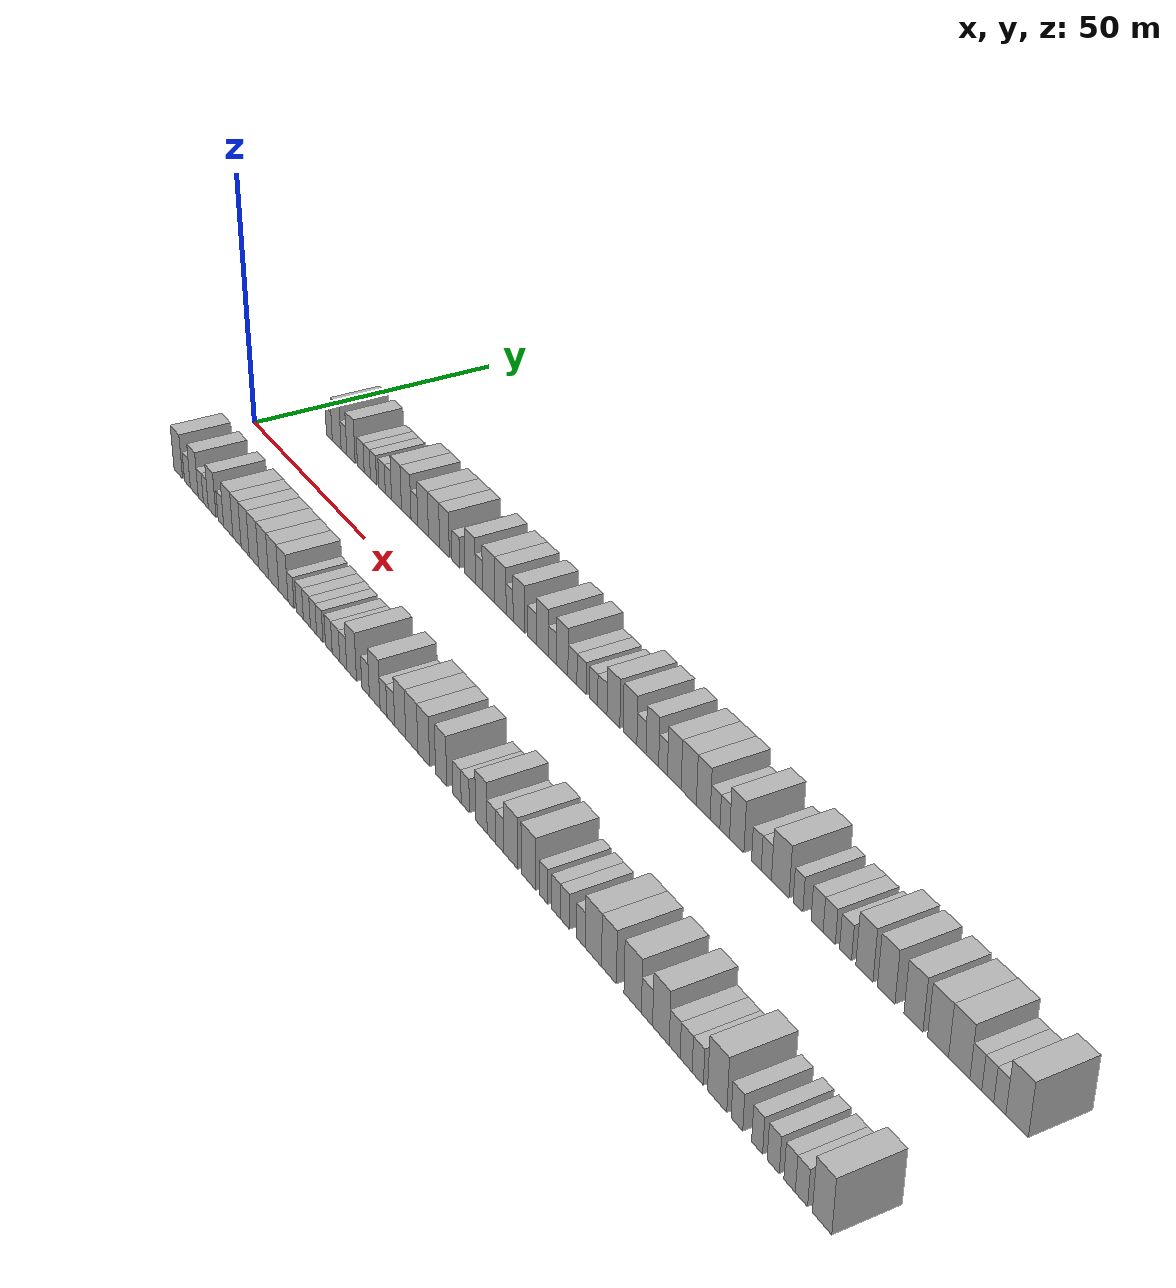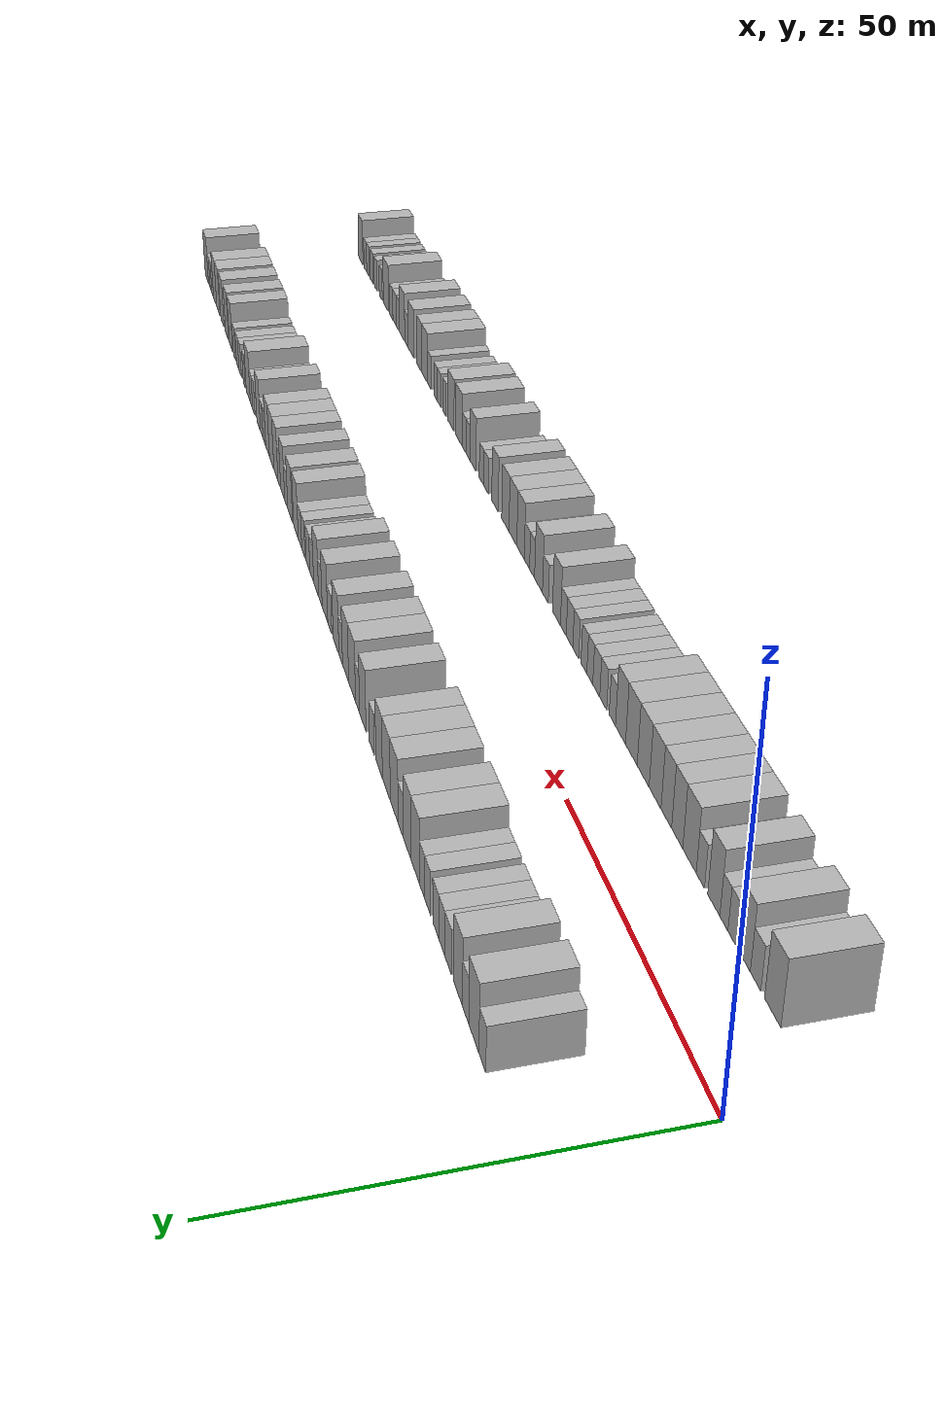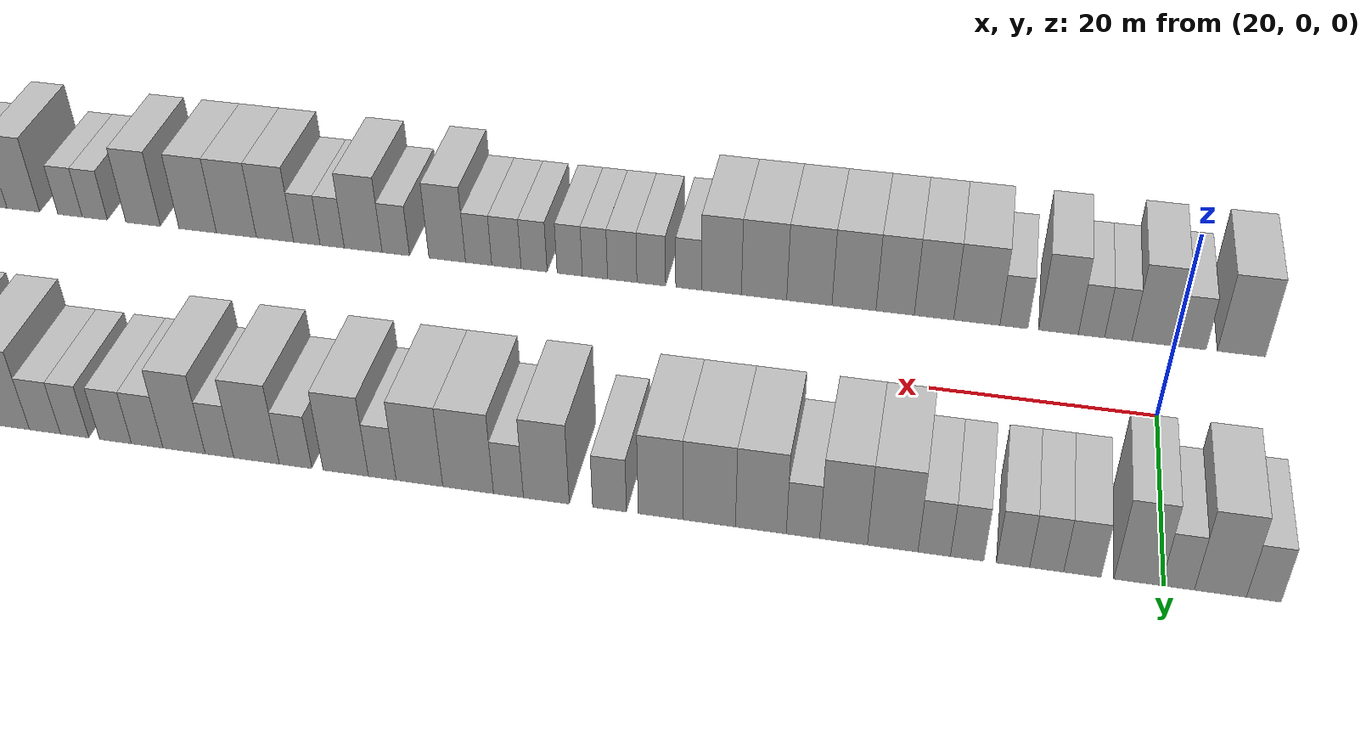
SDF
<sdf version="1.6">
 <world name="default">
  <scene>
   <sky><clouds><speed>12</speed></clouds></sky>
   <ambient>0.4 0.4 0.4 1</ambient>
   <background>0.7 0.7 0.7 1</background>
   <shadows>1</shadows>
  </scene>
  <gravity>0 0 -9.8066</gravity>
  <magnetic_field>6e-06 2.3e-05 -4.2e-05</magnetic_field>
  <physics default="0" name="default_physics" type="ode">
   <ode>
    <solver>
     <type>quick</type>
     <iters>10</iters>
     <sor>1.0</sor>
     <use_dynamic_moi_rescaling>0</use_dynamic_moi_rescaling>
    </solver>
    <constraints>
     <cfm>0</cfm>
     <erp>0.2</erp>
     <contact_max_correcting_vel>100</contact_max_correcting_vel>
     <contact_surface_layer>0.001</contact_surface_layer>
    </constraints>
   </ode>
   <max_step_size>0.004</max_step_size>
   <real_time_factor>1</real_time_factor>
   <real_time_update_rate>250</real_time_update_rate>
  </physics>
  <light name="sun" type="directional">
   <pose>0 0 10 0 0 0</pose>
   <diffuse>0.8 0.8 0.8 1</diffuse>
   <specular>0.2 0.2 0.2 1</specular>
   <attenuation>
    <range>1000</range>
    <constant>0.9</constant>
    <linear>0.01</linear>
    <quadratic>0.001</quadratic>
   </attenuation>
   <direction>-0.5 0.1 -0.9</direction>
  </light>
  <model name="building_1">
   <static>1</static>
   <pose>12.3237 15.0000 0 0.000000 0.000000 1.570796</pose>
   <link name="link">
    <pose>0 0 3.00 0 0 0</pose>
    <collision name="collision"><geometry><box><size>10.0000 2.6474 6.0000</size></box></geometry></collision>
    <visual name="visual">
     <cast_shadows>0</cast_shadows>
     <geometry><box><size>10.0000 2.6474 6.0000</size></box></geometry>
     <material>
      <script>
       <uri>model://HANNAS_wall/materials/scripts</uri>
       <uri>model://HANNAS_wall/materials/textures</uri>
       <name>vrc/HANNAS_wall</name>
      </script>
     </material>
    </visual>
   </link>
  </model>
  <model name="building_2">
   <static>1</static>
   <pose>15.6544 15.0000 0 0.000000 0.000000 1.570796</pose>
   <link name="link">
    <pose>0 0 4.50 0 0 0</pose>
    <collision name="collision"><geometry><box><size>10.0000 4.0139 9.0000</size></box></geometry></collision>
    <visual name="visual">
     <cast_shadows>0</cast_shadows>
     <geometry><box><size>10.0000 4.0139 9.0000</size></box></geometry>
     <material>
      <script>
       <uri>model://HANNAS_wall/materials/scripts</uri>
       <uri>model://HANNAS_wall/materials/textures</uri>
       <name>vrc/HANNAS_wall</name>
      </script>
     </material>
    </visual>
   </link>
  </model>
  <model name="building_3">
   <static>1</static>
   <pose>18.9484 15.0000 0 0.000000 0.000000 1.570796</pose>
   <link name="link">
    <pose>0 0 3.00 0 0 0</pose>
    <collision name="collision"><geometry><box><size>10.0000 2.5741 6.0000</size></box></geometry></collision>
    <visual name="visual">
     <cast_shadows>0</cast_shadows>
     <geometry><box><size>10.0000 2.5741 6.0000</size></box></geometry>
     <material>
      <script>
       <uri>model://HANNAS_wall/materials/scripts</uri>
       <uri>model://HANNAS_wall/materials/textures</uri>
       <name>vrc/HANNAS_wall</name>
      </script>
     </material>
    </visual>
   </link>
  </model>
  <model name="building_4">
   <static>1</static>
   <pose>22.0810 15.0000 0 0.000000 0.000000 1.570796</pose>
   <link name="link">
    <pose>0 0 4.50 0 0 0</pose>
    <collision name="collision"><geometry><box><size>10.0000 3.6913 9.0000</size></box></geometry></collision>
    <visual name="visual">
     <cast_shadows>0</cast_shadows>
     <geometry><box><size>10.0000 3.6913 9.0000</size></box></geometry>
     <material>
      <script>
       <uri>model://HANNAS_wall/materials/scripts</uri>
       <uri>model://HANNAS_wall/materials/textures</uri>
       <name>vrc/HANNAS_wall</name>
      </script>
     </material>
    </visual>
   </link>
  </model>
  <model name="building_5">
   <static>1</static>
   <pose>26.3997 15.0000 0 0.000000 0.000000 1.570796</pose>
   <link name="link">
    <pose>0 0 3.00 0 0 0</pose>
    <collision name="collision"><geometry><box><size>10.0000 2.9461 6.0000</size></box></geometry></collision>
    <visual name="visual">
     <cast_shadows>0</cast_shadows>
     <geometry><box><size>10.0000 2.9461 6.0000</size></box></geometry>
     <material>
      <script>
       <uri>model://HANNAS_wall/materials/scripts</uri>
       <uri>model://HANNAS_wall/materials/textures</uri>
       <name>vrc/HANNAS_wall</name>
      </script>
     </material>
    </visual>
   </link>
  </model>
  <model name="building_6">
   <static>1</static>
   <pose>29.2214 15.0000 0 0.000000 0.000000 1.570796</pose>
   <link name="link">
    <pose>0 0 3.00 0 0 0</pose>
    <collision name="collision"><geometry><box><size>10.0000 2.6973 6.0000</size></box></geometry></collision>
    <visual name="visual">
     <cast_shadows>0</cast_shadows>
     <geometry><box><size>10.0000 2.6973 6.0000</size></box></geometry>
     <material>
      <script>
       <uri>model://HANNAS_wall/materials/scripts</uri>
       <uri>model://HANNAS_wall/materials/textures</uri>
       <name>vrc/HANNAS_wall</name>
      </script>
     </material>
    </visual>
   </link>
  </model>
  <model name="building_7">
   <static>1</static>
   <pose>31.8918 15.0000 0 0.000000 0.000000 1.570796</pose>
   <link name="link">
    <pose>0 0 3.00 0 0 0</pose>
    <collision name="collision"><geometry><box><size>10.0000 2.6435 6.0000</size></box></geometry></collision>
    <visual name="visual">
     <cast_shadows>0</cast_shadows>
     <geometry><box><size>10.0000 2.6435 6.0000</size></box></geometry>
     <material>
      <script>
       <uri>model://HANNAS_wall/materials/scripts</uri>
       <uri>model://HANNAS_wall/materials/textures</uri>
       <name>vrc/HANNAS_wall</name>
      </script>
     </material>
    </visual>
   </link>
  </model>
  <model name="building_8">
   <static>1</static>
   <pose>35.5562 15.0000 0 0.000000 0.000000 1.570796</pose>
   <link name="link">
    <pose>0 0 3.00 0 0 0</pose>
    <collision name="collision"><geometry><box><size>10.0000 2.6854 6.0000</size></box></geometry></collision>
    <visual name="visual">
     <cast_shadows>0</cast_shadows>
     <geometry><box><size>10.0000 2.6854 6.0000</size></box></geometry>
     <material>
      <script>
       <uri>model://HANNAS_wall/materials/scripts</uri>
       <uri>model://HANNAS_wall/materials/textures</uri>
       <name>vrc/HANNAS_wall</name>
      </script>
     </material>
    </visual>
   </link>
  </model>
  <model name="building_9">
   <static>1</static>
   <pose>38.2074 15.0000 0 0.000000 0.000000 1.570796</pose>
   <link name="link">
    <pose>0 0 3.00 0 0 0</pose>
    <collision name="collision"><geometry><box><size>10.0000 2.6171 6.0000</size></box></geometry></collision>
    <visual name="visual">
     <cast_shadows>0</cast_shadows>
     <geometry><box><size>10.0000 2.6171 6.0000</size></box></geometry>
     <material>
      <script>
       <uri>model://HANNAS_wall/materials/scripts</uri>
       <uri>model://HANNAS_wall/materials/textures</uri>
       <name>vrc/HANNAS_wall</name>
      </script>
     </material>
    </visual>
   </link>
  </model>
  <model name="building_10">
   <static>1</static>
   <pose>41.5692 15.0000 0 0.000000 0.000000 1.570796</pose>
   <link name="link">
    <pose>0 0 4.50 0 0 0</pose>
    <collision name="collision"><geometry><box><size>10.0000 4.1065 9.0000</size></box></geometry></collision>
    <visual name="visual">
     <cast_shadows>0</cast_shadows>
     <geometry><box><size>10.0000 4.1065 9.0000</size></box></geometry>
     <material>
      <script>
       <uri>model://HANNAS_wall/materials/scripts</uri>
       <uri>model://HANNAS_wall/materials/textures</uri>
       <name>vrc/HANNAS_wall</name>
      </script>
     </material>
    </visual>
   </link>
  </model>
  <model name="building_11">
   <static>1</static>
   <pose>45.5778 15.0000 0 0.000000 0.000000 1.570796</pose>
   <link name="link">
    <pose>0 0 4.50 0 0 0</pose>
    <collision name="collision"><geometry><box><size>10.0000 3.9108 9.0000</size></box></geometry></collision>
    <visual name="visual">
     <cast_shadows>0</cast_shadows>
     <geometry><box><size>10.0000 3.9108 9.0000</size></box></geometry>
     <material>
      <script>
       <uri>model://HANNAS_wall/materials/scripts</uri>
       <uri>model://HANNAS_wall/materials/textures</uri>
       <name>vrc/HANNAS_wall</name>
      </script>
     </material>
    </visual>
   </link>
  </model>
  <model name="building_12">
   <static>1</static>
   <pose>48.9108 15.0000 0 0.000000 0.000000 1.570796</pose>
   <link name="link">
    <pose>0 0 3.00 0 0 0</pose>
    <collision name="collision"><geometry><box><size>10.0000 2.7551 6.0000</size></box></geometry></collision>
    <visual name="visual">
     <cast_shadows>0</cast_shadows>
     <geometry><box><size>10.0000 2.7551 6.0000</size></box></geometry>
     <material>
      <script>
       <uri>model://HANNAS_wall/materials/scripts</uri>
       <uri>model://HANNAS_wall/materials/textures</uri>
       <name>vrc/HANNAS_wall</name>
      </script>
     </material>
    </visual>
   </link>
  </model>
  <model name="building_13">
   <static>1</static>
   <pose>52.4000 15.0000 0 0.000000 0.000000 1.570796</pose>
   <link name="link">
    <pose>0 0 4.50 0 0 0</pose>
    <collision name="collision"><geometry><box><size>10.0000 4.2232 9.0000</size></box></geometry></collision>
    <visual name="visual">
     <cast_shadows>0</cast_shadows>
     <geometry><box><size>10.0000 4.2232 9.0000</size></box></geometry>
     <material>
      <script>
       <uri>model://HANNAS_wall/materials/scripts</uri>
       <uri>model://HANNAS_wall/materials/textures</uri>
       <name>vrc/HANNAS_wall</name>
      </script>
     </material>
    </visual>
   </link>
  </model>
  <model name="building_14">
   <static>1</static>
   <pose>56.7198 15.0000 0 0.000000 0.000000 1.570796</pose>
   <link name="link">
    <pose>0 0 4.50 0 0 0</pose>
    <collision name="collision"><geometry><box><size>10.0000 4.4164 9.0000</size></box></geometry></collision>
    <visual name="visual">
     <cast_shadows>0</cast_shadows>
     <geometry><box><size>10.0000 4.4164 9.0000</size></box></geometry>
     <material>
      <script>
       <uri>model://HANNAS_wall/materials/scripts</uri>
       <uri>model://HANNAS_wall/materials/textures</uri>
       <name>vrc/HANNAS_wall</name>
      </script>
     </material>
    </visual>
   </link>
  </model>
  <model name="building_15">
   <static>1</static>
   <pose>60.7979 15.0000 0 0.000000 0.000000 1.570796</pose>
   <link name="link">
    <pose>0 0 4.50 0 0 0</pose>
    <collision name="collision"><geometry><box><size>10.0000 3.7398 9.0000</size></box></geometry></collision>
    <visual name="visual">
     <cast_shadows>0</cast_shadows>
     <geometry><box><size>10.0000 3.7398 9.0000</size></box></geometry>
     <material>
      <script>
       <uri>model://HANNAS_wall/materials/scripts</uri>
       <uri>model://HANNAS_wall/materials/textures</uri>
       <name>vrc/HANNAS_wall</name>
      </script>
     </material>
    </visual>
   </link>
  </model>
  <model name="building_16">
   <static>1</static>
   <pose>65.1097 15.0000 0 0.000000 0.000000 1.570796</pose>
   <link name="link">
    <pose>0 0 3.00 0 0 0</pose>
    <collision name="collision"><geometry><box><size>10.0000 2.8838 6.0000</size></box></geometry></collision>
    <visual name="visual">
     <cast_shadows>0</cast_shadows>
     <geometry><box><size>10.0000 2.8838 6.0000</size></box></geometry>
     <material>
      <script>
       <uri>model://HANNAS_wall/materials/scripts</uri>
       <uri>model://HANNAS_wall/materials/textures</uri>
       <name>vrc/HANNAS_wall</name>
      </script>
     </material>
    </visual>
   </link>
  </model>
  <model name="building_17">
   <static>1</static>
   <pose>70.5278 15.0000 0 0.000000 0.000000 1.570796</pose>
   <link name="link">
    <pose>0 0 4.50 0 0 0</pose>
    <collision name="collision"><geometry><box><size>10.0000 3.9525 9.0000</size></box></geometry></collision>
    <visual name="visual">
     <cast_shadows>0</cast_shadows>
     <geometry><box><size>10.0000 3.9525 9.0000</size></box></geometry>
     <material>
      <script>
       <uri>model://HANNAS_wall/materials/scripts</uri>
       <uri>model://HANNAS_wall/materials/textures</uri>
       <name>vrc/HANNAS_wall</name>
      </script>
     </material>
    </visual>
   </link>
  </model>
  <model name="building_18">
   <static>1</static>
   <pose>73.7992 15.0000 0 0.000000 0.000000 1.570796</pose>
   <link name="link">
    <pose>0 0 3.00 0 0 0</pose>
    <collision name="collision"><geometry><box><size>10.0000 2.5903 6.0000</size></box></geometry></collision>
    <visual name="visual">
     <cast_shadows>0</cast_shadows>
     <geometry><box><size>10.0000 2.5903 6.0000</size></box></geometry>
     <material>
      <script>
       <uri>model://HANNAS_wall/materials/scripts</uri>
       <uri>model://HANNAS_wall/materials/textures</uri>
       <name>vrc/HANNAS_wall</name>
      </script>
     </material>
    </visual>
   </link>
  </model>
  <model name="building_19">
   <static>1</static>
   <pose>77.3071 15.0000 0 0.000000 0.000000 1.570796</pose>
   <link name="link">
    <pose>0 0 4.50 0 0 0</pose>
    <collision name="collision"><geometry><box><size>10.0000 4.4255 9.0000</size></box></geometry></collision>
    <visual name="visual">
     <cast_shadows>0</cast_shadows>
     <geometry><box><size>10.0000 4.4255 9.0000</size></box></geometry>
     <material>
      <script>
       <uri>model://HANNAS_wall/materials/scripts</uri>
       <uri>model://HANNAS_wall/materials/textures</uri>
       <name>vrc/HANNAS_wall</name>
      </script>
     </material>
    </visual>
   </link>
  </model>
  <model name="building_20">
   <static>1</static>
   <pose>81.5744 15.0000 0 0.000000 0.000000 1.570796</pose>
   <link name="link">
    <pose>0 0 4.50 0 0 0</pose>
    <collision name="collision"><geometry><box><size>10.0000 4.1091 9.0000</size></box></geometry></collision>
    <visual name="visual">
     <cast_shadows>0</cast_shadows>
     <geometry><box><size>10.0000 4.1091 9.0000</size></box></geometry>
     <material>
      <script>
       <uri>model://HANNAS_wall/materials/scripts</uri>
       <uri>model://HANNAS_wall/materials/textures</uri>
       <name>vrc/HANNAS_wall</name>
      </script>
     </material>
    </visual>
   </link>
  </model>
  <model name="building_21">
   <static>1</static>
   <pose>84.8576 15.0000 0 0.000000 0.000000 1.570796</pose>
   <link name="link">
    <pose>0 0 3.00 0 0 0</pose>
    <collision name="collision"><geometry><box><size>10.0000 2.4574 6.0000</size></box></geometry></collision>
    <visual name="visual">
     <cast_shadows>0</cast_shadows>
     <geometry><box><size>10.0000 2.4574 6.0000</size></box></geometry>
     <material>
      <script>
       <uri>model://HANNAS_wall/materials/scripts</uri>
       <uri>model://HANNAS_wall/materials/textures</uri>
       <name>vrc/HANNAS_wall</name>
      </script>
     </material>
    </visual>
   </link>
  </model>
  <model name="building_22">
   <static>1</static>
   <pose>88.1054 15.0000 0 0.000000 0.000000 1.570796</pose>
   <link name="link">
    <pose>0 0 4.50 0 0 0</pose>
    <collision name="collision"><geometry><box><size>10.0000 4.0382 9.0000</size></box></geometry></collision>
    <visual name="visual">
     <cast_shadows>0</cast_shadows>
     <geometry><box><size>10.0000 4.0382 9.0000</size></box></geometry>
     <material>
      <script>
       <uri>model://HANNAS_wall/materials/scripts</uri>
       <uri>model://HANNAS_wall/materials/textures</uri>
       <name>vrc/HANNAS_wall</name>
      </script>
     </material>
    </visual>
   </link>
  </model>
  <model name="building_23">
   <static>1</static>
   <pose>92.5916 15.0000 0 0.000000 0.000000 1.570796</pose>
   <link name="link">
    <pose>0 0 3.00 0 0 0</pose>
    <collision name="collision"><geometry><box><size>10.0000 2.9342 6.0000</size></box></geometry></collision>
    <visual name="visual">
     <cast_shadows>0</cast_shadows>
     <geometry><box><size>10.0000 2.9342 6.0000</size></box></geometry>
     <material>
      <script>
       <uri>model://HANNAS_wall/materials/scripts</uri>
       <uri>model://HANNAS_wall/materials/textures</uri>
       <name>vrc/HANNAS_wall</name>
      </script>
     </material>
    </visual>
   </link>
  </model>
  <model name="building_24">
   <static>1</static>
   <pose>96.1244 15.0000 0 0.000000 0.000000 1.570796</pose>
   <link name="link">
    <pose>0 0 4.50 0 0 0</pose>
    <collision name="collision"><geometry><box><size>10.0000 4.1314 9.0000</size></box></geometry></collision>
    <visual name="visual">
     <cast_shadows>0</cast_shadows>
     <geometry><box><size>10.0000 4.1314 9.0000</size></box></geometry>
     <material>
      <script>
       <uri>model://HANNAS_wall/materials/scripts</uri>
       <uri>model://HANNAS_wall/materials/textures</uri>
       <name>vrc/HANNAS_wall</name>
      </script>
     </material>
    </visual>
   </link>
  </model>
  <model name="building_25">
   <static>1</static>
   <pose>99.4918 15.0000 0 0.000000 0.000000 1.570796</pose>
   <link name="link">
    <pose>0 0 3.00 0 0 0</pose>
    <collision name="collision"><geometry><box><size>10.0000 2.6035 6.0000</size></box></geometry></collision>
    <visual name="visual">
     <cast_shadows>0</cast_shadows>
     <geometry><box><size>10.0000 2.6035 6.0000</size></box></geometry>
     <material>
      <script>
       <uri>model://HANNAS_wall/materials/scripts</uri>
       <uri>model://HANNAS_wall/materials/textures</uri>
       <name>vrc/HANNAS_wall</name>
      </script>
     </material>
    </visual>
   </link>
  </model>
  <model name="building_26">
   <static>1</static>
   <pose>102.7264 15.0000 0 0.000000 0.000000 1.570796</pose>
   <link name="link">
    <pose>0 0 4.50 0 0 0</pose>
    <collision name="collision"><geometry><box><size>10.0000 3.8657 9.0000</size></box></geometry></collision>
    <visual name="visual">
     <cast_shadows>0</cast_shadows>
     <geometry><box><size>10.0000 3.8657 9.0000</size></box></geometry>
     <material>
      <script>
       <uri>model://HANNAS_wall/materials/scripts</uri>
       <uri>model://HANNAS_wall/materials/textures</uri>
       <name>vrc/HANNAS_wall</name>
      </script>
     </material>
    </visual>
   </link>
  </model>
  <model name="building_27">
   <static>1</static>
   <pose>106.1207 15.0000 0 0.000000 0.000000 1.570796</pose>
   <link name="link">
    <pose>0 0 3.00 0 0 0</pose>
    <collision name="collision"><geometry><box><size>10.0000 2.9230 6.0000</size></box></geometry></collision>
    <visual name="visual">
     <cast_shadows>0</cast_shadows>
     <geometry><box><size>10.0000 2.9230 6.0000</size></box></geometry>
     <material>
      <script>
       <uri>model://HANNAS_wall/materials/scripts</uri>
       <uri>model://HANNAS_wall/materials/textures</uri>
       <name>vrc/HANNAS_wall</name>
      </script>
     </material>
    </visual>
   </link>
  </model>
  <model name="building_28">
   <static>1</static>
   <pose>109.0614 15.0000 0 0.000000 0.000000 1.570796</pose>
   <link name="link">
    <pose>0 0 3.00 0 0 0</pose>
    <collision name="collision"><geometry><box><size>10.0000 2.9583 6.0000</size></box></geometry></collision>
    <visual name="visual">
     <cast_shadows>0</cast_shadows>
     <geometry><box><size>10.0000 2.9583 6.0000</size></box></geometry>
     <material>
      <script>
       <uri>model://HANNAS_wall/materials/scripts</uri>
       <uri>model://HANNAS_wall/materials/textures</uri>
       <name>vrc/HANNAS_wall</name>
      </script>
     </material>
    </visual>
   </link>
  </model>
  <model name="building_29">
   <static>1</static>
   <pose>112.8695 15.0000 0 0.000000 0.000000 1.570796</pose>
   <link name="link">
    <pose>0 0 3.00 0 0 0</pose>
    <collision name="collision"><geometry><box><size>10.0000 2.6580 6.0000</size></box></geometry></collision>
    <visual name="visual">
     <cast_shadows>0</cast_shadows>
     <geometry><box><size>10.0000 2.6580 6.0000</size></box></geometry>
     <material>
      <script>
       <uri>model://HANNAS_wall/materials/scripts</uri>
       <uri>model://HANNAS_wall/materials/textures</uri>
       <name>vrc/HANNAS_wall</name>
      </script>
     </material>
    </visual>
   </link>
  </model>
  <model name="building_30">
   <static>1</static>
   <pose>115.6552 15.0000 0 0.000000 0.000000 1.570796</pose>
   <link name="link">
    <pose>0 0 3.00 0 0 0</pose>
    <collision name="collision"><geometry><box><size>10.0000 2.9134 6.0000</size></box></geometry></collision>
    <visual name="visual">
     <cast_shadows>0</cast_shadows>
     <geometry><box><size>10.0000 2.9134 6.0000</size></box></geometry>
     <material>
      <script>
       <uri>model://HANNAS_wall/materials/scripts</uri>
       <uri>model://HANNAS_wall/materials/textures</uri>
       <name>vrc/HANNAS_wall</name>
      </script>
     </material>
    </visual>
   </link>
  </model>
  <model name="building_31">
   <static>1</static>
   <pose>119.0930 15.0000 0 0.000000 0.000000 1.570796</pose>
   <link name="link">
    <pose>0 0 4.50 0 0 0</pose>
    <collision name="collision"><geometry><box><size>10.0000 3.9621 9.0000</size></box></geometry></collision>
    <visual name="visual">
     <cast_shadows>0</cast_shadows>
     <geometry><box><size>10.0000 3.9621 9.0000</size></box></geometry>
     <material>
      <script>
       <uri>model://HANNAS_wall/materials/scripts</uri>
       <uri>model://HANNAS_wall/materials/textures</uri>
       <name>vrc/HANNAS_wall</name>
      </script>
     </material>
    </visual>
   </link>
  </model>
  <model name="building_32">
   <static>1</static>
   <pose>124.1526 15.0000 0 0.000000 0.000000 1.570796</pose>
   <link name="link">
    <pose>0 0 4.50 0 0 0</pose>
    <collision name="collision"><geometry><box><size>10.0000 4.1572 9.0000</size></box></geometry></collision>
    <visual name="visual">
     <cast_shadows>0</cast_shadows>
     <geometry><box><size>10.0000 4.1572 9.0000</size></box></geometry>
     <material>
      <script>
       <uri>model://HANNAS_wall/materials/scripts</uri>
       <uri>model://HANNAS_wall/materials/textures</uri>
       <name>vrc/HANNAS_wall</name>
      </script>
     </material>
    </visual>
   </link>
  </model>
  <model name="building_33">
   <static>1</static>
   <pose>127.5959 15.0000 0 0.000000 0.000000 1.570796</pose>
   <link name="link">
    <pose>0 0 3.00 0 0 0</pose>
    <collision name="collision"><geometry><box><size>10.0000 2.7294 6.0000</size></box></geometry></collision>
    <visual name="visual">
     <cast_shadows>0</cast_shadows>
     <geometry><box><size>10.0000 2.7294 6.0000</size></box></geometry>
     <material>
      <script>
       <uri>model://HANNAS_wall/materials/scripts</uri>
       <uri>model://HANNAS_wall/materials/textures</uri>
       <name>vrc/HANNAS_wall</name>
      </script>
     </material>
    </visual>
   </link>
  </model>
  <model name="building_34">
   <static>1</static>
   <pose>130.8069 15.0000 0 0.000000 0.000000 1.570796</pose>
   <link name="link">
    <pose>0 0 4.50 0 0 0</pose>
    <collision name="collision"><geometry><box><size>10.0000 3.6927 9.0000</size></box></geometry></collision>
    <visual name="visual">
     <cast_shadows>0</cast_shadows>
     <geometry><box><size>10.0000 3.6927 9.0000</size></box></geometry>
     <material>
      <script>
       <uri>model://HANNAS_wall/materials/scripts</uri>
       <uri>model://HANNAS_wall/materials/textures</uri>
       <name>vrc/HANNAS_wall</name>
      </script>
     </material>
    </visual>
   </link>
  </model>
  <model name="building_35">
   <static>1</static>
   <pose>133.9190 15.0000 0 0.000000 0.000000 1.570796</pose>
   <link name="link">
    <pose>0 0 3.00 0 0 0</pose>
    <collision name="collision"><geometry><box><size>10.0000 2.5314 6.0000</size></box></geometry></collision>
    <visual name="visual">
     <cast_shadows>0</cast_shadows>
     <geometry><box><size>10.0000 2.5314 6.0000</size></box></geometry>
     <material>
      <script>
       <uri>model://HANNAS_wall/materials/scripts</uri>
       <uri>model://HANNAS_wall/materials/textures</uri>
       <name>vrc/HANNAS_wall</name>
      </script>
     </material>
    </visual>
   </link>
  </model>
  <model name="building_36">
   <static>1</static>
   <pose>137.1407 15.0000 0 0.000000 0.000000 1.570796</pose>
   <link name="link">
    <pose>0 0 4.50 0 0 0</pose>
    <collision name="collision"><geometry><box><size>10.0000 3.9121 9.0000</size></box></geometry></collision>
    <visual name="visual">
     <cast_shadows>0</cast_shadows>
     <geometry><box><size>10.0000 3.9121 9.0000</size></box></geometry>
     <material>
      <script>
       <uri>model://HANNAS_wall/materials/scripts</uri>
       <uri>model://HANNAS_wall/materials/textures</uri>
       <name>vrc/HANNAS_wall</name>
      </script>
     </material>
    </visual>
   </link>
  </model>
  <model name="building_37">
   <static>1</static>
   <pose>141.2572 15.0000 0 0.000000 0.000000 1.570796</pose>
   <link name="link">
    <pose>0 0 4.50 0 0 0</pose>
    <collision name="collision"><geometry><box><size>10.0000 4.3211 9.0000</size></box></geometry></collision>
    <visual name="visual">
     <cast_shadows>0</cast_shadows>
     <geometry><box><size>10.0000 4.3211 9.0000</size></box></geometry>
     <material>
      <script>
       <uri>model://HANNAS_wall/materials/scripts</uri>
       <uri>model://HANNAS_wall/materials/textures</uri>
       <name>vrc/HANNAS_wall</name>
      </script>
     </material>
    </visual>
   </link>
  </model>
  <model name="building_38">
   <static>1</static>
   <pose>145.3111 15.0000 0 0.000000 0.000000 1.570796</pose>
   <link name="link">
    <pose>0 0 4.50 0 0 0</pose>
    <collision name="collision"><geometry><box><size>10.0000 3.7867 9.0000</size></box></geometry></collision>
    <visual name="visual">
     <cast_shadows>0</cast_shadows>
     <geometry><box><size>10.0000 3.7867 9.0000</size></box></geometry>
     <material>
      <script>
       <uri>model://HANNAS_wall/materials/scripts</uri>
       <uri>model://HANNAS_wall/materials/textures</uri>
       <name>vrc/HANNAS_wall</name>
      </script>
     </material>
    </visual>
   </link>
  </model>
  <model name="building_39">
   <static>1</static>
   <pose>148.5455 15.0000 0 0.000000 0.000000 1.570796</pose>
   <link name="link">
    <pose>0 0 3.00 0 0 0</pose>
    <collision name="collision"><geometry><box><size>10.0000 2.6821 6.0000</size></box></geometry></collision>
    <visual name="visual">
     <cast_shadows>0</cast_shadows>
     <geometry><box><size>10.0000 2.6821 6.0000</size></box></geometry>
     <material>
      <script>
       <uri>model://HANNAS_wall/materials/scripts</uri>
       <uri>model://HANNAS_wall/materials/textures</uri>
       <name>vrc/HANNAS_wall</name>
      </script>
     </material>
    </visual>
   </link>
  </model>
  <model name="building_40">
   <static>1</static>
   <pose>151.1820 15.0000 0 0.000000 0.000000 1.570796</pose>
   <link name="link">
    <pose>0 0 3.00 0 0 0</pose>
    <collision name="collision"><geometry><box><size>10.0000 2.5909 6.0000</size></box></geometry></collision>
    <visual name="visual">
     <cast_shadows>0</cast_shadows>
     <geometry><box><size>10.0000 2.5909 6.0000</size></box></geometry>
     <material>
      <script>
       <uri>model://HANNAS_wall/materials/scripts</uri>
       <uri>model://HANNAS_wall/materials/textures</uri>
       <name>vrc/HANNAS_wall</name>
      </script>
     </material>
    </visual>
   </link>
  </model>
  <model name="building_41">
   <static>1</static>
   <pose>154.3863 15.0000 0 0.000000 0.000000 1.570796</pose>
   <link name="link">
    <pose>0 0 4.50 0 0 0</pose>
    <collision name="collision"><geometry><box><size>10.0000 3.8178 9.0000</size></box></geometry></collision>
    <visual name="visual">
     <cast_shadows>0</cast_shadows>
     <geometry><box><size>10.0000 3.8178 9.0000</size></box></geometry>
     <material>
      <script>
       <uri>model://HANNAS_wall/materials/scripts</uri>
       <uri>model://HANNAS_wall/materials/textures</uri>
       <name>vrc/HANNAS_wall</name>
      </script>
     </material>
    </visual>
   </link>
  </model>
  <model name="building_42">
   <static>1</static>
   <pose>159.5500 15.0000 0 0.000000 0.000000 1.570796</pose>
   <link name="link">
    <pose>0 0 3.00 0 0 0</pose>
    <collision name="collision"><geometry><box><size>10.0000 2.5095 6.0000</size></box></geometry></collision>
    <visual name="visual">
     <cast_shadows>0</cast_shadows>
     <geometry><box><size>10.0000 2.5095 6.0000</size></box></geometry>
     <material>
      <script>
       <uri>model://HANNAS_wall/materials/scripts</uri>
       <uri>model://HANNAS_wall/materials/textures</uri>
       <name>vrc/HANNAS_wall</name>
      </script>
     </material>
    </visual>
   </link>
  </model>
  <model name="building_43">
   <static>1</static>
   <pose>162.1150 15.0000 0 0.000000 0.000000 1.570796</pose>
   <link name="link">
    <pose>0 0 3.00 0 0 0</pose>
    <collision name="collision"><geometry><box><size>10.0000 2.6204 6.0000</size></box></geometry></collision>
    <visual name="visual">
     <cast_shadows>0</cast_shadows>
     <geometry><box><size>10.0000 2.6204 6.0000</size></box></geometry>
     <material>
      <script>
       <uri>model://HANNAS_wall/materials/scripts</uri>
       <uri>model://HANNAS_wall/materials/textures</uri>
       <name>vrc/HANNAS_wall</name>
      </script>
     </material>
    </visual>
   </link>
  </model>
  <model name="building_44">
   <static>1</static>
   <pose>165.6594 15.0000 0 0.000000 0.000000 1.570796</pose>
   <link name="link">
    <pose>0 0 4.50 0 0 0</pose>
    <collision name="collision"><geometry><box><size>10.0000 4.4684 9.0000</size></box></geometry></collision>
    <visual name="visual">
     <cast_shadows>0</cast_shadows>
     <geometry><box><size>10.0000 4.4684 9.0000</size></box></geometry>
     <material>
      <script>
       <uri>model://HANNAS_wall/materials/scripts</uri>
       <uri>model://HANNAS_wall/materials/textures</uri>
       <name>vrc/HANNAS_wall</name>
      </script>
     </material>
    </visual>
   </link>
  </model>
  <model name="building_45">
   <static>1</static>
   <pose>170.1038 15.0000 0 0.000000 0.000000 1.570796</pose>
   <link name="link">
    <pose>0 0 3.00 0 0 0</pose>
    <collision name="collision"><geometry><box><size>10.0000 2.4204 6.0000</size></box></geometry></collision>
    <visual name="visual">
     <cast_shadows>0</cast_shadows>
     <geometry><box><size>10.0000 2.4204 6.0000</size></box></geometry>
     <material>
      <script>
       <uri>model://HANNAS_wall/materials/scripts</uri>
       <uri>model://HANNAS_wall/materials/textures</uri>
       <name>vrc/HANNAS_wall</name>
      </script>
     </material>
    </visual>
   </link>
  </model>
  <model name="building_46">
   <static>1</static>
   <pose>174.7673 15.0000 0 0.000000 0.000000 1.570796</pose>
   <link name="link">
    <pose>0 0 3.00 0 0 0</pose>
    <collision name="collision"><geometry><box><size>10.0000 2.9066 6.0000</size></box></geometry></collision>
    <visual name="visual">
     <cast_shadows>0</cast_shadows>
     <geometry><box><size>10.0000 2.9066 6.0000</size></box></geometry>
     <material>
      <script>
       <uri>model://HANNAS_wall/materials/scripts</uri>
       <uri>model://HANNAS_wall/materials/textures</uri>
       <name>vrc/HANNAS_wall</name>
      </script>
     </material>
    </visual>
   </link>
  </model>
  <model name="building_47">
   <static>1</static>
   <pose>177.6863 15.0000 0 0.000000 0.000000 1.570796</pose>
   <link name="link">
    <pose>0 0 3.00 0 0 0</pose>
    <collision name="collision"><geometry><box><size>10.0000 2.9313 6.0000</size></box></geometry></collision>
    <visual name="visual">
     <cast_shadows>0</cast_shadows>
     <geometry><box><size>10.0000 2.9313 6.0000</size></box></geometry>
     <material>
      <script>
       <uri>model://HANNAS_wall/materials/scripts</uri>
       <uri>model://HANNAS_wall/materials/textures</uri>
       <name>vrc/HANNAS_wall</name>
      </script>
     </material>
    </visual>
   </link>
  </model>
  <model name="building_48">
   <static>1</static>
   <pose>181.5532 15.0000 0 0.000000 0.000000 1.570796</pose>
   <link name="link">
    <pose>0 0 3.00 0 0 0</pose>
    <collision name="collision"><geometry><box><size>10.0000 2.8025 6.0000</size></box></geometry></collision>
    <visual name="visual">
     <cast_shadows>0</cast_shadows>
     <geometry><box><size>10.0000 2.8025 6.0000</size></box></geometry>
     <material>
      <script>
       <uri>model://HANNAS_wall/materials/scripts</uri>
       <uri>model://HANNAS_wall/materials/textures</uri>
       <name>vrc/HANNAS_wall</name>
      </script>
     </material>
    </visual>
   </link>
  </model>
  <model name="building_49">
   <static>1</static>
   <pose>185.9270 15.0000 0 0.000000 0.000000 1.570796</pose>
   <link name="link">
    <pose>0 0 4.50 0 0 0</pose>
    <collision name="collision"><geometry><box><size>10.0000 3.9450 9.0000</size></box></geometry></collision>
    <visual name="visual">
     <cast_shadows>0</cast_shadows>
     <geometry><box><size>10.0000 3.9450 9.0000</size></box></geometry>
     <material>
      <script>
       <uri>model://HANNAS_wall/materials/scripts</uri>
       <uri>model://HANNAS_wall/materials/textures</uri>
       <name>vrc/HANNAS_wall</name>
      </script>
     </material>
    </visual>
   </link>
  </model>
  <model name="building_50">
   <static>1</static>
   <pose>190.8726 15.0000 0 0.000000 0.000000 1.570796</pose>
   <link name="link">
    <pose>0 0 4.50 0 0 0</pose>
    <collision name="collision"><geometry><box><size>10.0000 3.9462 9.0000</size></box></geometry></collision>
    <visual name="visual">
     <cast_shadows>0</cast_shadows>
     <geometry><box><size>10.0000 3.9462 9.0000</size></box></geometry>
     <material>
      <script>
       <uri>model://HANNAS_wall/materials/scripts</uri>
       <uri>model://HANNAS_wall/materials/textures</uri>
       <name>vrc/HANNAS_wall</name>
      </script>
     </material>
    </visual>
   </link>
  </model>
  <model name="building_51">
   <static>1</static>
   <pose>196.9149 15.0000 0 0.000000 0.000000 1.570796</pose>
   <link name="link">
    <pose>0 0 4.50 0 0 0</pose>
    <collision name="collision"><geometry><box><size>10.0000 4.1385 9.0000</size></box></geometry></collision>
    <visual name="visual">
     <cast_shadows>0</cast_shadows>
     <geometry><box><size>10.0000 4.1385 9.0000</size></box></geometry>
     <material>
      <script>
       <uri>model://HANNAS_wall/materials/scripts</uri>
       <uri>model://HANNAS_wall/materials/textures</uri>
       <name>vrc/HANNAS_wall</name>
      </script>
     </material>
    </visual>
   </link>
  </model>
  <model name="building_52">
   <static>1</static>
   <pose>202.2018 15.0000 0 0.000000 0.000000 1.570796</pose>
   <link name="link">
    <pose>0 0 4.50 0 0 0</pose>
    <collision name="collision"><geometry><box><size>10.0000 4.4352 9.0000</size></box></geometry></collision>
    <visual name="visual">
     <cast_shadows>0</cast_shadows>
     <geometry><box><size>10.0000 4.4352 9.0000</size></box></geometry>
     <material>
      <script>
       <uri>model://HANNAS_wall/materials/scripts</uri>
       <uri>model://HANNAS_wall/materials/textures</uri>
       <name>vrc/HANNAS_wall</name>
      </script>
     </material>
    </visual>
   </link>
  </model>
  <model name="building_53">
   <static>1</static>
   <pose>206.6403 15.0000 0 0.000000 0.000000 1.570796</pose>
   <link name="link">
    <pose>0 0 4.50 0 0 0</pose>
    <collision name="collision"><geometry><box><size>10.0000 4.4420 9.0000</size></box></geometry></collision>
    <visual name="visual">
     <cast_shadows>0</cast_shadows>
     <geometry><box><size>10.0000 4.4420 9.0000</size></box></geometry>
     <material>
      <script>
       <uri>model://HANNAS_wall/materials/scripts</uri>
       <uri>model://HANNAS_wall/materials/textures</uri>
       <name>vrc/HANNAS_wall</name>
      </script>
     </material>
    </visual>
   </link>
  </model>
  <model name="building_54">
   <static>1</static>
   <pose>210.0744 15.0000 0 0.000000 0.000000 1.570796</pose>
   <link name="link">
    <pose>0 0 3.00 0 0 0</pose>
    <collision name="collision"><geometry><box><size>10.0000 2.4262 6.0000</size></box></geometry></collision>
    <visual name="visual">
     <cast_shadows>0</cast_shadows>
     <geometry><box><size>10.0000 2.4262 6.0000</size></box></geometry>
     <material>
      <script>
       <uri>model://HANNAS_wall/materials/scripts</uri>
       <uri>model://HANNAS_wall/materials/textures</uri>
       <name>vrc/HANNAS_wall</name>
      </script>
     </material>
    </visual>
   </link>
  </model>
  <model name="building_55">
   <static>1</static>
   <pose>212.4924 15.0000 0 0.000000 0.000000 1.570796</pose>
   <link name="link">
    <pose>0 0 3.00 0 0 0</pose>
    <collision name="collision"><geometry><box><size>10.0000 2.4098 6.0000</size></box></geometry></collision>
    <visual name="visual">
     <cast_shadows>0</cast_shadows>
     <geometry><box><size>10.0000 2.4098 6.0000</size></box></geometry>
     <material>
      <script>
       <uri>model://HANNAS_wall/materials/scripts</uri>
       <uri>model://HANNAS_wall/materials/textures</uri>
       <name>vrc/HANNAS_wall</name>
      </script>
     </material>
    </visual>
   </link>
  </model>
  <model name="building_56">
   <static>1</static>
   <pose>214.9073 15.0000 0 0.000000 0.000000 1.570796</pose>
   <link name="link">
    <pose>0 0 3.00 0 0 0</pose>
    <collision name="collision"><geometry><box><size>10.0000 2.4200 6.0000</size></box></geometry></collision>
    <visual name="visual">
     <cast_shadows>0</cast_shadows>
     <geometry><box><size>10.0000 2.4200 6.0000</size></box></geometry>
     <material>
      <script>
       <uri>model://HANNAS_wall/materials/scripts</uri>
       <uri>model://HANNAS_wall/materials/textures</uri>
       <name>vrc/HANNAS_wall</name>
      </script>
     </material>
    </visual>
   </link>
  </model>
  <model name="building_57">
   <static>1</static>
   <pose>218.3203 15.0000 0 0.000000 0.000000 1.570796</pose>
   <link name="link">
    <pose>0 0 4.50 0 0 0</pose>
    <collision name="collision"><geometry><box><size>10.0000 4.4059 9.0000</size></box></geometry></collision>
    <visual name="visual">
     <cast_shadows>0</cast_shadows>
     <geometry><box><size>10.0000 4.4059 9.0000</size></box></geometry>
     <material>
      <script>
       <uri>model://HANNAS_wall/materials/scripts</uri>
       <uri>model://HANNAS_wall/materials/textures</uri>
       <name>vrc/HANNAS_wall</name>
      </script>
     </material>
    </visual>
   </link>
  </model>
  <model name="building_58">
   <static>1</static>
   <pose>12.1530 -15.0000 0 0.000000 0.000000 1.570796</pose>
   <link name="link">
    <pose>0 0 4.50 0 0 0</pose>
    <collision name="collision"><geometry><box><size>10.0000 4.3059 9.0000</size></box></geometry></collision>
    <visual name="visual">
     <cast_shadows>0</cast_shadows>
     <geometry><box><size>10.0000 4.3059 9.0000</size></box></geometry>
     <material>
      <script>
       <uri>model://HANNAS_wall/materials/scripts</uri>
       <uri>model://HANNAS_wall/materials/textures</uri>
       <name>vrc/HANNAS_wall</name>
      </script>
     </material>
    </visual>
   </link>
  </model>
  <model name="building_59">
   <static>1</static>
   <pose>16.7434 -15.0000 0 0.000000 0.000000 1.570796</pose>
   <link name="link">
    <pose>0 0 3.00 0 0 0</pose>
    <collision name="collision"><geometry><box><size>10.0000 2.8750 6.0000</size></box></geometry></collision>
    <visual name="visual">
     <cast_shadows>0</cast_shadows>
     <geometry><box><size>10.0000 2.8750 6.0000</size></box></geometry>
     <material>
      <script>
       <uri>model://HANNAS_wall/materials/scripts</uri>
       <uri>model://HANNAS_wall/materials/textures</uri>
       <name>vrc/HANNAS_wall</name>
      </script>
     </material>
    </visual>
   </link>
  </model>
  <model name="building_60">
   <static>1</static>
   <pose>20.1097 -15.0000 0 0.000000 0.000000 1.570796</pose>
   <link name="link">
    <pose>0 0 4.50 0 0 0</pose>
    <collision name="collision"><geometry><box><size>10.0000 3.8575 9.0000</size></box></geometry></collision>
    <visual name="visual">
     <cast_shadows>0</cast_shadows>
     <geometry><box><size>10.0000 3.8575 9.0000</size></box></geometry>
     <material>
      <script>
       <uri>model://HANNAS_wall/materials/scripts</uri>
       <uri>model://HANNAS_wall/materials/textures</uri>
       <name>vrc/HANNAS_wall</name>
      </script>
     </material>
    </visual>
   </link>
  </model>
  <model name="building_61">
   <static>1</static>
   <pose>23.2841 -15.0000 0 0.000000 0.000000 1.570796</pose>
   <link name="link">
    <pose>0 0 3.00 0 0 0</pose>
    <collision name="collision"><geometry><box><size>10.0000 2.4914 6.0000</size></box></geometry></collision>
    <visual name="visual">
     <cast_shadows>0</cast_shadows>
     <geometry><box><size>10.0000 2.4914 6.0000</size></box></geometry>
     <material>
      <script>
       <uri>model://HANNAS_wall/materials/scripts</uri>
       <uri>model://HANNAS_wall/materials/textures</uri>
       <name>vrc/HANNAS_wall</name>
      </script>
     </material>
    </visual>
   </link>
  </model>
  <model name="building_62">
   <static>1</static>
   <pose>25.7311 -15.0000 0 0.000000 0.000000 1.570796</pose>
   <link name="link">
    <pose>0 0 3.00 0 0 0</pose>
    <collision name="collision"><geometry><box><size>10.0000 2.4025 6.0000</size></box></geometry></collision>
    <visual name="visual">
     <cast_shadows>0</cast_shadows>
     <geometry><box><size>10.0000 2.4025 6.0000</size></box></geometry>
     <material>
      <script>
       <uri>model://HANNAS_wall/materials/scripts</uri>
       <uri>model://HANNAS_wall/materials/textures</uri>
       <name>vrc/HANNAS_wall</name>
      </script>
     </material>
    </visual>
   </link>
  </model>
  <model name="building_63">
   <static>1</static>
   <pose>28.7611 -15.0000 0 0.000000 0.000000 1.570796</pose>
   <link name="link">
    <pose>0 0 4.50 0 0 0</pose>
    <collision name="collision"><geometry><box><size>10.0000 3.6576 9.0000</size></box></geometry></collision>
    <visual name="visual">
     <cast_shadows>0</cast_shadows>
     <geometry><box><size>10.0000 3.6576 9.0000</size></box></geometry>
     <material>
      <script>
       <uri>model://HANNAS_wall/materials/scripts</uri>
       <uri>model://HANNAS_wall/materials/textures</uri>
       <name>vrc/HANNAS_wall</name>
      </script>
     </material>
    </visual>
   </link>
  </model>
  <model name="building_64">
   <static>1</static>
   <pose>32.8890 -15.0000 0 0.000000 0.000000 1.570796</pose>
   <link name="link">
    <pose>0 0 3.00 0 0 0</pose>
    <collision name="collision"><geometry><box><size>10.0000 2.5982 6.0000</size></box></geometry></collision>
    <visual name="visual">
     <cast_shadows>0</cast_shadows>
     <geometry><box><size>10.0000 2.5982 6.0000</size></box></geometry>
     <material>
      <script>
       <uri>model://HANNAS_wall/materials/scripts</uri>
       <uri>model://HANNAS_wall/materials/textures</uri>
       <name>vrc/HANNAS_wall</name>
      </script>
     </material>
    </visual>
   </link>
  </model>
  <model name="building_65">
   <static>1</static>
   <pose>36.3493 -15.0000 0 0.000000 0.000000 1.570796</pose>
   <link name="link">
    <pose>0 0 4.50 0 0 0</pose>
    <collision name="collision"><geometry><box><size>10.0000 4.3224 9.0000</size></box></geometry></collision>
    <visual name="visual">
     <cast_shadows>0</cast_shadows>
     <geometry><box><size>10.0000 4.3224 9.0000</size></box></geometry>
     <material>
      <script>
       <uri>model://HANNAS_wall/materials/scripts</uri>
       <uri>model://HANNAS_wall/materials/textures</uri>
       <name>vrc/HANNAS_wall</name>
      </script>
     </material>
    </visual>
   </link>
  </model>
  <model name="building_66">
   <static>1</static>
   <pose>40.3686 -15.0000 0 0.000000 0.000000 1.570796</pose>
   <link name="link">
    <pose>0 0 4.50 0 0 0</pose>
    <collision name="collision"><geometry><box><size>10.0000 3.7162 9.0000</size></box></geometry></collision>
    <visual name="visual">
     <cast_shadows>0</cast_shadows>
     <geometry><box><size>10.0000 3.7162 9.0000</size></box></geometry>
     <material>
      <script>
       <uri>model://HANNAS_wall/materials/scripts</uri>
       <uri>model://HANNAS_wall/materials/textures</uri>
       <name>vrc/HANNAS_wall</name>
      </script>
     </material>
    </visual>
   </link>
  </model>
  <model name="building_67">
   <static>1</static>
   <pose>44.0421 -15.0000 0 0.000000 0.000000 1.570796</pose>
   <link name="link">
    <pose>0 0 4.50 0 0 0</pose>
    <collision name="collision"><geometry><box><size>10.0000 3.6307 9.0000</size></box></geometry></collision>
    <visual name="visual">
     <cast_shadows>0</cast_shadows>
     <geometry><box><size>10.0000 3.6307 9.0000</size></box></geometry>
     <material>
      <script>
       <uri>model://HANNAS_wall/materials/scripts</uri>
       <uri>model://HANNAS_wall/materials/textures</uri>
       <name>vrc/HANNAS_wall</name>
      </script>
     </material>
    </visual>
   </link>
  </model>
  <model name="building_68">
   <static>1</static>
   <pose>47.9543 -15.0000 0 0.000000 0.000000 1.570796</pose>
   <link name="link">
    <pose>0 0 4.50 0 0 0</pose>
    <collision name="collision"><geometry><box><size>10.0000 4.1936 9.0000</size></box></geometry></collision>
    <visual name="visual">
     <cast_shadows>0</cast_shadows>
     <geometry><box><size>10.0000 4.1936 9.0000</size></box></geometry>
     <material>
      <script>
       <uri>model://HANNAS_wall/materials/scripts</uri>
       <uri>model://HANNAS_wall/materials/textures</uri>
       <name>vrc/HANNAS_wall</name>
      </script>
     </material>
    </visual>
   </link>
  </model>
  <model name="building_69">
   <static>1</static>
   <pose>52.2260 -15.0000 0 0.000000 0.000000 1.570796</pose>
   <link name="link">
    <pose>0 0 4.50 0 0 0</pose>
    <collision name="collision"><geometry><box><size>10.0000 4.3500 9.0000</size></box></geometry></collision>
    <visual name="visual">
     <cast_shadows>0</cast_shadows>
     <geometry><box><size>10.0000 4.3500 9.0000</size></box></geometry>
     <material>
      <script>
       <uri>model://HANNAS_wall/materials/scripts</uri>
       <uri>model://HANNAS_wall/materials/textures</uri>
       <name>vrc/HANNAS_wall</name>
      </script>
     </material>
    </visual>
   </link>
  </model>
  <model name="building_70">
   <static>1</static>
   <pose>56.5990 -15.0000 0 0.000000 0.000000 1.570796</pose>
   <link name="link">
    <pose>0 0 4.50 0 0 0</pose>
    <collision name="collision"><geometry><box><size>10.0000 4.3959 9.0000</size></box></geometry></collision>
    <visual name="visual">
     <cast_shadows>0</cast_shadows>
     <geometry><box><size>10.0000 4.3959 9.0000</size></box></geometry>
     <material>
      <script>
       <uri>model://HANNAS_wall/materials/scripts</uri>
       <uri>model://HANNAS_wall/materials/textures</uri>
       <name>vrc/HANNAS_wall</name>
      </script>
     </material>
    </visual>
   </link>
  </model>
  <model name="building_71">
   <static>1</static>
   <pose>60.7470 -15.0000 0 0.000000 0.000000 1.570796</pose>
   <link name="link">
    <pose>0 0 4.50 0 0 0</pose>
    <collision name="collision"><geometry><box><size>10.0000 3.9002 9.0000</size></box></geometry></collision>
    <visual name="visual">
     <cast_shadows>0</cast_shadows>
     <geometry><box><size>10.0000 3.9002 9.0000</size></box></geometry>
     <material>
      <script>
       <uri>model://HANNAS_wall/materials/scripts</uri>
       <uri>model://HANNAS_wall/materials/textures</uri>
       <name>vrc/HANNAS_wall</name>
      </script>
     </material>
    </visual>
   </link>
  </model>
  <model name="building_72">
   <static>1</static>
   <pose>63.9483 -15.0000 0 0.000000 0.000000 1.570796</pose>
   <link name="link">
    <pose>0 0 3.00 0 0 0</pose>
    <collision name="collision"><geometry><box><size>10.0000 2.5024 6.0000</size></box></geometry></collision>
    <visual name="visual">
     <cast_shadows>0</cast_shadows>
     <geometry><box><size>10.0000 2.5024 6.0000</size></box></geometry>
     <material>
      <script>
       <uri>model://HANNAS_wall/materials/scripts</uri>
       <uri>model://HANNAS_wall/materials/textures</uri>
       <name>vrc/HANNAS_wall</name>
      </script>
     </material>
    </visual>
   </link>
  </model>
  <model name="building_73">
   <static>1</static>
   <pose>67.6168 -15.0000 0 0.000000 0.000000 1.570796</pose>
   <link name="link">
    <pose>0 0 3.00 0 0 0</pose>
    <collision name="collision"><geometry><box><size>10.0000 2.8345 6.0000</size></box></geometry></collision>
    <visual name="visual">
     <cast_shadows>0</cast_shadows>
     <geometry><box><size>10.0000 2.8345 6.0000</size></box></geometry>
     <material>
      <script>
       <uri>model://HANNAS_wall/materials/scripts</uri>
       <uri>model://HANNAS_wall/materials/textures</uri>
       <name>vrc/HANNAS_wall</name>
      </script>
     </material>
    </visual>
   </link>
  </model>
  <model name="building_74">
   <static>1</static>
   <pose>70.4877 -15.0000 0 0.000000 0.000000 1.570796</pose>
   <link name="link">
    <pose>0 0 3.00 0 0 0</pose>
    <collision name="collision"><geometry><box><size>10.0000 2.9074 6.0000</size></box></geometry></collision>
    <visual name="visual">
     <cast_shadows>0</cast_shadows>
     <geometry><box><size>10.0000 2.9074 6.0000</size></box></geometry>
     <material>
      <script>
       <uri>model://HANNAS_wall/materials/scripts</uri>
       <uri>model://HANNAS_wall/materials/textures</uri>
       <name>vrc/HANNAS_wall</name>
      </script>
     </material>
    </visual>
   </link>
  </model>
  <model name="building_75">
   <static>1</static>
   <pose>73.1978 -15.0000 0 0.000000 0.000000 1.570796</pose>
   <link name="link">
    <pose>0 0 3.00 0 0 0</pose>
    <collision name="collision"><geometry><box><size>10.0000 2.5127 6.0000</size></box></geometry></collision>
    <visual name="visual">
     <cast_shadows>0</cast_shadows>
     <geometry><box><size>10.0000 2.5127 6.0000</size></box></geometry>
     <material>
      <script>
       <uri>model://HANNAS_wall/materials/scripts</uri>
       <uri>model://HANNAS_wall/materials/textures</uri>
       <name>vrc/HANNAS_wall</name>
      </script>
     </material>
    </visual>
   </link>
  </model>
  <model name="building_76">
   <static>1</static>
   <pose>75.7167 -15.0000 0 0.000000 0.000000 1.570796</pose>
   <link name="link">
    <pose>0 0 3.00 0 0 0</pose>
    <collision name="collision"><geometry><box><size>10.0000 2.5252 6.0000</size></box></geometry></collision>
    <visual name="visual">
     <cast_shadows>0</cast_shadows>
     <geometry><box><size>10.0000 2.5252 6.0000</size></box></geometry>
     <material>
      <script>
       <uri>model://HANNAS_wall/materials/scripts</uri>
       <uri>model://HANNAS_wall/materials/textures</uri>
       <name>vrc/HANNAS_wall</name>
      </script>
     </material>
    </visual>
   </link>
  </model>
  <model name="building_77">
   <static>1</static>
   <pose>79.2878 -15.0000 0 0.000000 0.000000 1.570796</pose>
   <link name="link">
    <pose>0 0 3.00 0 0 0</pose>
    <collision name="collision"><geometry><box><size>10.0000 2.6170 6.0000</size></box></geometry></collision>
    <visual name="visual">
     <cast_shadows>0</cast_shadows>
     <geometry><box><size>10.0000 2.6170 6.0000</size></box></geometry>
     <material>
      <script>
       <uri>model://HANNAS_wall/materials/scripts</uri>
       <uri>model://HANNAS_wall/materials/textures</uri>
       <name>vrc/HANNAS_wall</name>
      </script>
     </material>
    </visual>
   </link>
  </model>
  <model name="building_78">
   <static>1</static>
   <pose>82.0816 -15.0000 0 0.000000 0.000000 1.570796</pose>
   <link name="link">
    <pose>0 0 3.00 0 0 0</pose>
    <collision name="collision"><geometry><box><size>10.0000 2.9705 6.0000</size></box></geometry></collision>
    <visual name="visual">
     <cast_shadows>0</cast_shadows>
     <geometry><box><size>10.0000 2.9705 6.0000</size></box></geometry>
     <material>
      <script>
       <uri>model://HANNAS_wall/materials/scripts</uri>
       <uri>model://HANNAS_wall/materials/textures</uri>
       <name>vrc/HANNAS_wall</name>
      </script>
     </material>
    </visual>
   </link>
  </model>
  <model name="building_79">
   <static>1</static>
   <pose>84.9033 -15.0000 0 0.000000 0.000000 1.570796</pose>
   <link name="link">
    <pose>0 0 3.00 0 0 0</pose>
    <collision name="collision"><geometry><box><size>10.0000 2.6730 6.0000</size></box></geometry></collision>
    <visual name="visual">
     <cast_shadows>0</cast_shadows>
     <geometry><box><size>10.0000 2.6730 6.0000</size></box></geometry>
     <material>
      <script>
       <uri>model://HANNAS_wall/materials/scripts</uri>
       <uri>model://HANNAS_wall/materials/textures</uri>
       <name>vrc/HANNAS_wall</name>
      </script>
     </material>
    </visual>
   </link>
  </model>
  <model name="building_80">
   <static>1</static>
   <pose>88.1082 -15.0000 0 0.000000 0.000000 1.570796</pose>
   <link name="link">
    <pose>0 0 4.50 0 0 0</pose>
    <collision name="collision"><geometry><box><size>10.0000 3.7370 9.0000</size></box></geometry></collision>
    <visual name="visual">
     <cast_shadows>0</cast_shadows>
     <geometry><box><size>10.0000 3.7370 9.0000</size></box></geometry>
     <material>
      <script>
       <uri>model://HANNAS_wall/materials/scripts</uri>
       <uri>model://HANNAS_wall/materials/textures</uri>
       <name>vrc/HANNAS_wall</name>
      </script>
     </material>
    </visual>
   </link>
  </model>
  <model name="building_81">
   <static>1</static>
   <pose>93.3863 -15.0000 0 0.000000 0.000000 1.570796</pose>
   <link name="link">
    <pose>0 0 3.00 0 0 0</pose>
    <collision name="collision"><geometry><box><size>10.0000 2.8192 6.0000</size></box></geometry></collision>
    <visual name="visual">
     <cast_shadows>0</cast_shadows>
     <geometry><box><size>10.0000 2.8192 6.0000</size></box></geometry>
     <material>
      <script>
       <uri>model://HANNAS_wall/materials/scripts</uri>
       <uri>model://HANNAS_wall/materials/textures</uri>
       <name>vrc/HANNAS_wall</name>
      </script>
     </material>
    </visual>
   </link>
  </model>
  <model name="building_82">
   <static>1</static>
   <pose>96.7603 -15.0000 0 0.000000 0.000000 1.570796</pose>
   <link name="link">
    <pose>0 0 4.50 0 0 0</pose>
    <collision name="collision"><geometry><box><size>10.0000 3.9289 9.0000</size></box></geometry></collision>
    <visual name="visual">
     <cast_shadows>0</cast_shadows>
     <geometry><box><size>10.0000 3.9289 9.0000</size></box></geometry>
     <material>
      <script>
       <uri>model://HANNAS_wall/materials/scripts</uri>
       <uri>model://HANNAS_wall/materials/textures</uri>
       <name>vrc/HANNAS_wall</name>
      </script>
     </material>
    </visual>
   </link>
  </model>
  <model name="building_83">
   <static>1</static>
   <pose>99.9871 -15.0000 0 0.000000 0.000000 1.570796</pose>
   <link name="link">
    <pose>0 0 3.00 0 0 0</pose>
    <collision name="collision"><geometry><box><size>10.0000 2.5247 6.0000</size></box></geometry></collision>
    <visual name="visual">
     <cast_shadows>0</cast_shadows>
     <geometry><box><size>10.0000 2.5247 6.0000</size></box></geometry>
     <material>
      <script>
       <uri>model://HANNAS_wall/materials/scripts</uri>
       <uri>model://HANNAS_wall/materials/textures</uri>
       <name>vrc/HANNAS_wall</name>
      </script>
     </material>
    </visual>
   </link>
  </model>
  <model name="building_84">
   <static>1</static>
   <pose>102.6329 -15.0000 0 0.000000 0.000000 1.570796</pose>
   <link name="link">
    <pose>0 0 3.00 0 0 0</pose>
    <collision name="collision"><geometry><box><size>10.0000 2.7668 6.0000</size></box></geometry></collision>
    <visual name="visual">
     <cast_shadows>0</cast_shadows>
     <geometry><box><size>10.0000 2.7668 6.0000</size></box></geometry>
     <material>
      <script>
       <uri>model://HANNAS_wall/materials/scripts</uri>
       <uri>model://HANNAS_wall/materials/textures</uri>
       <name>vrc/HANNAS_wall</name>
      </script>
     </material>
    </visual>
   </link>
  </model>
  <model name="building_85">
   <static>1</static>
   <pose>105.9797 -15.0000 0 0.000000 0.000000 1.570796</pose>
   <link name="link">
    <pose>0 0 4.50 0 0 0</pose>
    <collision name="collision"><geometry><box><size>10.0000 3.9270 9.0000</size></box></geometry></collision>
    <visual name="visual">
     <cast_shadows>0</cast_shadows>
     <geometry><box><size>10.0000 3.9270 9.0000</size></box></geometry>
     <material>
      <script>
       <uri>model://HANNAS_wall/materials/scripts</uri>
       <uri>model://HANNAS_wall/materials/textures</uri>
       <name>vrc/HANNAS_wall</name>
      </script>
     </material>
    </visual>
   </link>
  </model>
  <model name="building_86">
   <static>1</static>
   <pose>110.0636 -15.0000 0 0.000000 0.000000 1.570796</pose>
   <link name="link">
    <pose>0 0 4.50 0 0 0</pose>
    <collision name="collision"><geometry><box><size>10.0000 4.2408 9.0000</size></box></geometry></collision>
    <visual name="visual">
     <cast_shadows>0</cast_shadows>
     <geometry><box><size>10.0000 4.2408 9.0000</size></box></geometry>
     <material>
      <script>
       <uri>model://HANNAS_wall/materials/scripts</uri>
       <uri>model://HANNAS_wall/materials/textures</uri>
       <name>vrc/HANNAS_wall</name>
      </script>
     </material>
    </visual>
   </link>
  </model>
  <model name="building_87">
   <static>1</static>
   <pose>114.1880 -15.0000 0 0.000000 0.000000 1.570796</pose>
   <link name="link">
    <pose>0 0 4.50 0 0 0</pose>
    <collision name="collision"><geometry><box><size>10.0000 4.0079 9.0000</size></box></geometry></collision>
    <visual name="visual">
     <cast_shadows>0</cast_shadows>
     <geometry><box><size>10.0000 4.0079 9.0000</size></box></geometry>
     <material>
      <script>
       <uri>model://HANNAS_wall/materials/scripts</uri>
       <uri>model://HANNAS_wall/materials/textures</uri>
       <name>vrc/HANNAS_wall</name>
      </script>
     </material>
    </visual>
   </link>
  </model>
  <model name="building_88">
   <static>1</static>
   <pose>120.0512 -15.0000 0 0.000000 0.000000 1.570796</pose>
   <link name="link">
    <pose>0 0 4.50 0 0 0</pose>
    <collision name="collision"><geometry><box><size>10.0000 3.7185 9.0000</size></box></geometry></collision>
    <visual name="visual">
     <cast_shadows>0</cast_shadows>
     <geometry><box><size>10.0000 3.7185 9.0000</size></box></geometry>
     <material>
      <script>
       <uri>model://HANNAS_wall/materials/scripts</uri>
       <uri>model://HANNAS_wall/materials/textures</uri>
       <name>vrc/HANNAS_wall</name>
      </script>
     </material>
    </visual>
   </link>
  </model>
  <model name="building_89">
   <static>1</static>
   <pose>125.2764 -15.0000 0 0.000000 0.000000 1.570796</pose>
   <link name="link">
    <pose>0 0 3.00 0 0 0</pose>
    <collision name="collision"><geometry><box><size>10.0000 2.7319 6.0000</size></box></geometry></collision>
    <visual name="visual">
     <cast_shadows>0</cast_shadows>
     <geometry><box><size>10.0000 2.7319 6.0000</size></box></geometry>
     <material>
      <script>
       <uri>model://HANNAS_wall/materials/scripts</uri>
       <uri>model://HANNAS_wall/materials/textures</uri>
       <name>vrc/HANNAS_wall</name>
      </script>
     </material>
    </visual>
   </link>
  </model>
  <model name="building_90">
   <static>1</static>
   <pose>127.9747 -15.0000 0 0.000000 0.000000 1.570796</pose>
   <link name="link">
    <pose>0 0 3.00 0 0 0</pose>
    <collision name="collision"><geometry><box><size>10.0000 2.6647 6.0000</size></box></geometry></collision>
    <visual name="visual">
     <cast_shadows>0</cast_shadows>
     <geometry><box><size>10.0000 2.6647 6.0000</size></box></geometry>
     <material>
      <script>
       <uri>model://HANNAS_wall/materials/scripts</uri>
       <uri>model://HANNAS_wall/materials/textures</uri>
       <name>vrc/HANNAS_wall</name>
      </script>
     </material>
    </visual>
   </link>
  </model>
  <model name="building_91">
   <static>1</static>
   <pose>133.1096 -15.0000 0 0.000000 0.000000 1.570796</pose>
   <link name="link">
    <pose>0 0 4.50 0 0 0</pose>
    <collision name="collision"><geometry><box><size>10.0000 3.6052 9.0000</size></box></geometry></collision>
    <visual name="visual">
     <cast_shadows>0</cast_shadows>
     <geometry><box><size>10.0000 3.6052 9.0000</size></box></geometry>
     <material>
      <script>
       <uri>model://HANNAS_wall/materials/scripts</uri>
       <uri>model://HANNAS_wall/materials/textures</uri>
       <name>vrc/HANNAS_wall</name>
      </script>
     </material>
    </visual>
   </link>
  </model>
  <model name="building_92">
   <static>1</static>
   <pose>136.2700 -15.0000 0 0.000000 0.000000 1.570796</pose>
   <link name="link">
    <pose>0 0 3.00 0 0 0</pose>
    <collision name="collision"><geometry><box><size>10.0000 2.7156 6.0000</size></box></geometry></collision>
    <visual name="visual">
     <cast_shadows>0</cast_shadows>
     <geometry><box><size>10.0000 2.7156 6.0000</size></box></geometry>
     <material>
      <script>
       <uri>model://HANNAS_wall/materials/scripts</uri>
       <uri>model://HANNAS_wall/materials/textures</uri>
       <name>vrc/HANNAS_wall</name>
      </script>
     </material>
    </visual>
   </link>
  </model>
  <model name="building_93">
   <static>1</static>
   <pose>138.8516 -15.0000 0 0.000000 0.000000 1.570796</pose>
   <link name="link">
    <pose>0 0 3.00 0 0 0</pose>
    <collision name="collision"><geometry><box><size>10.0000 2.4476 6.0000</size></box></geometry></collision>
    <visual name="visual">
     <cast_shadows>0</cast_shadows>
     <geometry><box><size>10.0000 2.4476 6.0000</size></box></geometry>
     <material>
      <script>
       <uri>model://HANNAS_wall/materials/scripts</uri>
       <uri>model://HANNAS_wall/materials/textures</uri>
       <name>vrc/HANNAS_wall</name>
      </script>
     </material>
    </visual>
   </link>
  </model>
  <model name="building_94">
   <static>1</static>
   <pose>142.2176 -15.0000 0 0.000000 0.000000 1.570796</pose>
   <link name="link">
    <pose>0 0 4.50 0 0 0</pose>
    <collision name="collision"><geometry><box><size>10.0000 4.2845 9.0000</size></box></geometry></collision>
    <visual name="visual">
     <cast_shadows>0</cast_shadows>
     <geometry><box><size>10.0000 4.2845 9.0000</size></box></geometry>
     <material>
      <script>
       <uri>model://HANNAS_wall/materials/scripts</uri>
       <uri>model://HANNAS_wall/materials/textures</uri>
       <name>vrc/HANNAS_wall</name>
      </script>
     </material>
    </visual>
   </link>
  </model>
  <model name="building_95">
   <static>1</static>
   <pose>147.5184 -15.0000 0 0.000000 0.000000 1.570796</pose>
   <link name="link">
    <pose>0 0 4.50 0 0 0</pose>
    <collision name="collision"><geometry><box><size>10.0000 4.3171 9.0000</size></box></geometry></collision>
    <visual name="visual">
     <cast_shadows>0</cast_shadows>
     <geometry><box><size>10.0000 4.3171 9.0000</size></box></geometry>
     <material>
      <script>
       <uri>model://HANNAS_wall/materials/scripts</uri>
       <uri>model://HANNAS_wall/materials/textures</uri>
       <name>vrc/HANNAS_wall</name>
      </script>
     </material>
    </visual>
   </link>
  </model>
  <model name="building_96">
   <static>1</static>
   <pose>151.9259 -15.0000 0 0.000000 0.000000 1.570796</pose>
   <link name="link">
    <pose>0 0 3.00 0 0 0</pose>
    <collision name="collision"><geometry><box><size>10.0000 2.4979 6.0000</size></box></geometry></collision>
    <visual name="visual">
     <cast_shadows>0</cast_shadows>
     <geometry><box><size>10.0000 2.4979 6.0000</size></box></geometry>
     <material>
      <script>
       <uri>model://HANNAS_wall/materials/scripts</uri>
       <uri>model://HANNAS_wall/materials/textures</uri>
       <name>vrc/HANNAS_wall</name>
      </script>
     </material>
    </visual>
   </link>
  </model>
  <model name="building_97">
   <static>1</static>
   <pose>155.4397 -15.0000 0 0.000000 0.000000 1.570796</pose>
   <link name="link">
    <pose>0 0 3.00 0 0 0</pose>
    <collision name="collision"><geometry><box><size>10.0000 2.5298 6.0000</size></box></geometry></collision>
    <visual name="visual">
     <cast_shadows>0</cast_shadows>
     <geometry><box><size>10.0000 2.5298 6.0000</size></box></geometry>
     <material>
      <script>
       <uri>model://HANNAS_wall/materials/scripts</uri>
       <uri>model://HANNAS_wall/materials/textures</uri>
       <name>vrc/HANNAS_wall</name>
      </script>
     </material>
    </visual>
   </link>
  </model>
  <model name="building_98">
   <static>1</static>
   <pose>157.9842 -15.0000 0 0.000000 0.000000 1.570796</pose>
   <link name="link">
    <pose>0 0 3.00 0 0 0</pose>
    <collision name="collision"><geometry><box><size>10.0000 2.5592 6.0000</size></box></geometry></collision>
    <visual name="visual">
     <cast_shadows>0</cast_shadows>
     <geometry><box><size>10.0000 2.5592 6.0000</size></box></geometry>
     <material>
      <script>
       <uri>model://HANNAS_wall/materials/scripts</uri>
       <uri>model://HANNAS_wall/materials/textures</uri>
       <name>vrc/HANNAS_wall</name>
      </script>
     </material>
    </visual>
   </link>
  </model>
  <model name="building_99">
   <static>1</static>
   <pose>162.4889 -15.0000 0 0.000000 0.000000 1.570796</pose>
   <link name="link">
    <pose>0 0 3.00 0 0 0</pose>
    <collision name="collision"><geometry><box><size>10.0000 2.4500 6.0000</size></box></geometry></collision>
    <visual name="visual">
     <cast_shadows>0</cast_shadows>
     <geometry><box><size>10.0000 2.4500 6.0000</size></box></geometry>
     <material>
      <script>
       <uri>model://HANNAS_wall/materials/scripts</uri>
       <uri>model://HANNAS_wall/materials/textures</uri>
       <name>vrc/HANNAS_wall</name>
      </script>
     </material>
    </visual>
   </link>
  </model>
  <model name="building_100">
   <static>1</static>
   <pose>165.9148 -15.0000 0 0.000000 0.000000 1.570796</pose>
   <link name="link">
    <pose>0 0 4.50 0 0 0</pose>
    <collision name="collision"><geometry><box><size>10.0000 4.4018 9.0000</size></box></geometry></collision>
    <visual name="visual">
     <cast_shadows>0</cast_shadows>
     <geometry><box><size>10.0000 4.4018 9.0000</size></box></geometry>
     <material>
      <script>
       <uri>model://HANNAS_wall/materials/scripts</uri>
       <uri>model://HANNAS_wall/materials/textures</uri>
       <name>vrc/HANNAS_wall</name>
      </script>
     </material>
    </visual>
   </link>
  </model>
  <model name="building_101">
   <static>1</static>
   <pose>170.0994 -15.0000 0 0.000000 0.000000 1.570796</pose>
   <link name="link">
    <pose>0 0 4.50 0 0 0</pose>
    <collision name="collision"><geometry><box><size>10.0000 3.9675 9.0000</size></box></geometry></collision>
    <visual name="visual">
     <cast_shadows>0</cast_shadows>
     <geometry><box><size>10.0000 3.9675 9.0000</size></box></geometry>
     <material>
      <script>
       <uri>model://HANNAS_wall/materials/scripts</uri>
       <uri>model://HANNAS_wall/materials/textures</uri>
       <name>vrc/HANNAS_wall</name>
      </script>
     </material>
    </visual>
   </link>
  </model>
  <model name="building_102">
   <static>1</static>
   <pose>176.3247 -15.0000 0 0.000000 0.000000 1.570796</pose>
   <link name="link">
    <pose>0 0 4.50 0 0 0</pose>
    <collision name="collision"><geometry><box><size>10.0000 4.4831 9.0000</size></box></geometry></collision>
    <visual name="visual">
     <cast_shadows>0</cast_shadows>
     <geometry><box><size>10.0000 4.4831 9.0000</size></box></geometry>
     <material>
      <script>
       <uri>model://HANNAS_wall/materials/scripts</uri>
       <uri>model://HANNAS_wall/materials/textures</uri>
       <name>vrc/HANNAS_wall</name>
      </script>
     </material>
    </visual>
   </link>
  </model>
  <model name="building_103">
   <static>1</static>
   <pose>179.9890 -15.0000 0 0.000000 0.000000 1.570796</pose>
   <link name="link">
    <pose>0 0 3.00 0 0 0</pose>
    <collision name="collision"><geometry><box><size>10.0000 2.8454 6.0000</size></box></geometry></collision>
    <visual name="visual">
     <cast_shadows>0</cast_shadows>
     <geometry><box><size>10.0000 2.8454 6.0000</size></box></geometry>
     <material>
      <script>
       <uri>model://HANNAS_wall/materials/scripts</uri>
       <uri>model://HANNAS_wall/materials/textures</uri>
       <name>vrc/HANNAS_wall</name>
      </script>
     </material>
    </visual>
   </link>
  </model>
  <model name="building_104">
   <static>1</static>
   <pose>183.4970 -15.0000 0 0.000000 0.000000 1.570796</pose>
   <link name="link">
    <pose>0 0 4.50 0 0 0</pose>
    <collision name="collision"><geometry><box><size>10.0000 4.1706 9.0000</size></box></geometry></collision>
    <visual name="visual">
     <cast_shadows>0</cast_shadows>
     <geometry><box><size>10.0000 4.1706 9.0000</size></box></geometry>
     <material>
      <script>
       <uri>model://HANNAS_wall/materials/scripts</uri>
       <uri>model://HANNAS_wall/materials/textures</uri>
       <name>vrc/HANNAS_wall</name>
      </script>
     </material>
    </visual>
   </link>
  </model>
  <model name="building_105">
   <static>1</static>
   <pose>186.9197 -15.0000 0 0.000000 0.000000 1.570796</pose>
   <link name="link">
    <pose>0 0 3.00 0 0 0</pose>
    <collision name="collision"><geometry><box><size>10.0000 2.6746 6.0000</size></box></geometry></collision>
    <visual name="visual">
     <cast_shadows>0</cast_shadows>
     <geometry><box><size>10.0000 2.6746 6.0000</size></box></geometry>
     <material>
      <script>
       <uri>model://HANNAS_wall/materials/scripts</uri>
       <uri>model://HANNAS_wall/materials/textures</uri>
       <name>vrc/HANNAS_wall</name>
      </script>
     </material>
    </visual>
   </link>
  </model>
  <model name="building_106">
   <static>1</static>
   <pose>189.7164 -15.0000 0 0.000000 0.000000 1.570796</pose>
   <link name="link">
    <pose>0 0 3.00 0 0 0</pose>
    <collision name="collision"><geometry><box><size>10.0000 2.9188 6.0000</size></box></geometry></collision>
    <visual name="visual">
     <cast_shadows>0</cast_shadows>
     <geometry><box><size>10.0000 2.9188 6.0000</size></box></geometry>
     <material>
      <script>
       <uri>model://HANNAS_wall/materials/scripts</uri>
       <uri>model://HANNAS_wall/materials/textures</uri>
       <name>vrc/HANNAS_wall</name>
      </script>
     </material>
    </visual>
   </link>
  </model>
  <model name="building_107">
   <static>1</static>
   <pose>192.5179 -15.0000 0 0.000000 0.000000 1.570796</pose>
   <link name="link">
    <pose>0 0 3.00 0 0 0</pose>
    <collision name="collision"><geometry><box><size>10.0000 2.6842 6.0000</size></box></geometry></collision>
    <visual name="visual">
     <cast_shadows>0</cast_shadows>
     <geometry><box><size>10.0000 2.6842 6.0000</size></box></geometry>
     <material>
      <script>
       <uri>model://HANNAS_wall/materials/scripts</uri>
       <uri>model://HANNAS_wall/materials/textures</uri>
       <name>vrc/HANNAS_wall</name>
      </script>
     </material>
    </visual>
   </link>
  </model>
  <model name="building_108">
   <static>1</static>
   <pose>197.1072 -15.0000 0 0.000000 0.000000 1.570796</pose>
   <link name="link">
    <pose>0 0 4.50 0 0 0</pose>
    <collision name="collision"><geometry><box><size>10.0000 4.4944 9.0000</size></box></geometry></collision>
    <visual name="visual">
     <cast_shadows>0</cast_shadows>
     <geometry><box><size>10.0000 4.4944 9.0000</size></box></geometry>
     <material>
      <script>
       <uri>model://HANNAS_wall/materials/scripts</uri>
       <uri>model://HANNAS_wall/materials/textures</uri>
       <name>vrc/HANNAS_wall</name>
      </script>
     </material>
    </visual>
   </link>
  </model>
  <model name="building_109">
   <static>1</static>
   <pose>201.6840 -15.0000 0 0.000000 0.000000 1.570796</pose>
   <link name="link">
    <pose>0 0 3.00 0 0 0</pose>
    <collision name="collision"><geometry><box><size>10.0000 2.6592 6.0000</size></box></geometry></collision>
    <visual name="visual">
     <cast_shadows>0</cast_shadows>
     <geometry><box><size>10.0000 2.6592 6.0000</size></box></geometry>
     <material>
      <script>
       <uri>model://HANNAS_wall/materials/scripts</uri>
       <uri>model://HANNAS_wall/materials/textures</uri>
       <name>vrc/HANNAS_wall</name>
      </script>
     </material>
    </visual>
   </link>
  </model>
  <model name="building_110">
   <static>1</static>
   <pose>206.2373 -15.0000 0 0.000000 0.000000 1.570796</pose>
   <link name="link">
    <pose>0 0 3.00 0 0 0</pose>
    <collision name="collision"><geometry><box><size>10.0000 2.4474 6.0000</size></box></geometry></collision>
    <visual name="visual">
     <cast_shadows>0</cast_shadows>
     <geometry><box><size>10.0000 2.4474 6.0000</size></box></geometry>
     <material>
      <script>
       <uri>model://HANNAS_wall/materials/scripts</uri>
       <uri>model://HANNAS_wall/materials/textures</uri>
       <name>vrc/HANNAS_wall</name>
      </script>
     </material>
    </visual>
   </link>
  </model>
  <model name="building_111">
   <static>1</static>
   <pose>209.7883 -15.0000 0 0.000000 0.000000 1.570796</pose>
   <link name="link">
    <pose>0 0 3.00 0 0 0</pose>
    <collision name="collision"><geometry><box><size>10.0000 2.6545 6.0000</size></box></geometry></collision>
    <visual name="visual">
     <cast_shadows>0</cast_shadows>
     <geometry><box><size>10.0000 2.6545 6.0000</size></box></geometry>
     <material>
      <script>
       <uri>model://HANNAS_wall/materials/scripts</uri>
       <uri>model://HANNAS_wall/materials/textures</uri>
       <name>vrc/HANNAS_wall</name>
      </script>
     </material>
    </visual>
   </link>
  </model>
  <model name="building_112">
   <static>1</static>
   <pose>213.3446 -15.0000 0 0.000000 0.000000 1.570796</pose>
   <link name="link">
    <pose>0 0 3.00 0 0 0</pose>
    <collision name="collision"><geometry><box><size>10.0000 2.4581 6.0000</size></box></geometry></collision>
    <visual name="visual">
     <cast_shadows>0</cast_shadows>
     <geometry><box><size>10.0000 2.4581 6.0000</size></box></geometry>
     <material>
      <script>
       <uri>model://HANNAS_wall/materials/scripts</uri>
       <uri>model://HANNAS_wall/materials/textures</uri>
       <name>vrc/HANNAS_wall</name>
      </script>
     </material>
    </visual>
   </link>
  </model>
  <model name="building_113">
   <static>1</static>
   <pose>215.8762 -15.0000 0 0.000000 0.000000 1.570796</pose>
   <link name="link">
    <pose>0 0 3.00 0 0 0</pose>
    <collision name="collision"><geometry><box><size>10.0000 2.6050 6.0000</size></box></geometry></collision>
    <visual name="visual">
     <cast_shadows>0</cast_shadows>
     <geometry><box><size>10.0000 2.6050 6.0000</size></box></geometry>
     <material>
      <script>
       <uri>model://HANNAS_wall/materials/scripts</uri>
       <uri>model://HANNAS_wall/materials/textures</uri>
       <name>vrc/HANNAS_wall</name>
      </script>
     </material>
    </visual>
   </link>
  </model>
  <model name="building_114">
   <static>1</static>
   <pose>220.1916 -15.0000 0 0.000000 0.000000 1.570796</pose>
   <link name="link">
    <pose>0 0 4.50 0 0 0</pose>
    <collision name="collision"><geometry><box><size>10.0000 4.0259 9.0000</size></box></geometry></collision>
    <visual name="visual">
     <cast_shadows>0</cast_shadows>
     <geometry><box><size>10.0000 4.0259 9.0000</size></box></geometry>
     <material>
      <script>
       <uri>model://HANNAS_wall/materials/scripts</uri>
       <uri>model://HANNAS_wall/materials/textures</uri>
       <name>vrc/HANNAS_wall</name>
      </script>
     </material>
    </visual>
   </link>
  </model>
 </world>
</sdf>
